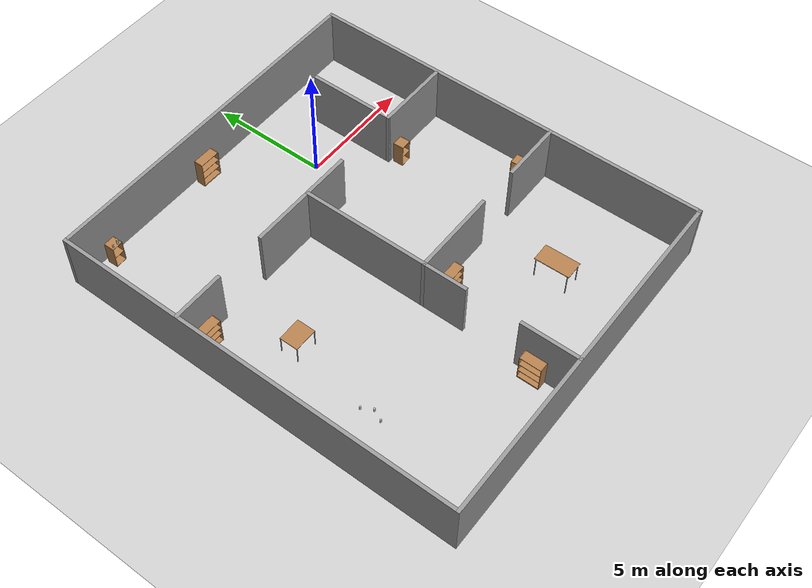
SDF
<sdf version="1.6">
 <world name="default">
  <physics name="default_physics" default="0" type="ode">
   <ode>
    <solver>
     <type>quick</type>
     <iters>20</iters>
     <sor>1</sor>
     <use_dynamic_moi_rescaling>0</use_dynamic_moi_rescaling>
    </solver>
    <constraints>
     <cfm>0</cfm>
     <erp>0.2</erp>
     <contact_max_correcting_vel>100</contact_max_correcting_vel>
     <contact_surface_layer>0</contact_surface_layer>
    </constraints>
   </ode>
   <real_time_update_rate>1000</real_time_update_rate>
   <max_step_size>0.001</max_step_size>
   <real_time_factor>1</real_time_factor>
   <max_contacts>20</max_contacts>
  </physics>
  <light name="sun" type="directional">
   <pose>0 0 10 0 -0 0</pose>
   <diffuse>0.8 0.8 0.8 1</diffuse>
   <specular>0.2 0.2 0.2 1</specular>
   <attenuation>
    <range>1000</range>
    <constant>0.9</constant>
    <linear>0.01</linear>
    <quadratic>0.001</quadratic>
   </attenuation>
   <direction>0.5 0.1 -0.9</direction>
  </light>
  <model name="ground_plane">
   <static>1</static>
   <link name="link">
    <collision name="collision">
     <geometry><plane><normal>0 0 1</normal><size>100 100</size></plane></geometry>
     <surface><friction><ode><mu>100</mu><mu2>50</mu2></ode></friction></surface>
    </collision>
    <visual name="visual">
     <cast_shadows>0</cast_shadows>
     <geometry><plane><normal>0 0 1</normal><size>100 100</size></plane></geometry>
     <material>
      <script><uri>file://media/materials/scripts/gazebo.material</uri><name>Gazebo/Grey</name></script>
     </material>
    </visual>
    <velocity_decay><linear>0</linear><angular>0</angular></velocity_decay>
   </link>
  </model>
  <scene><ambient>0.2 0.2 0.2 1</ambient><background>0.7 0.7 0.7 1</background><shadows>1</shadows></scene>
  <model name="cabinet">
   <static>0</static>
   <link name="cabinet_bottom_plate">
    <inertial>
     <pose>0 0 -1 0 -0 0</pose>
     <inertia><ixx>2.05</ixx><ixy>0</ixy><ixz>0</ixz><iyy>2.05</iyy><iyz>0</iyz><izz>2.05</izz></inertia>
     <mass>25</mass>
    </inertial>
    <collision name="cabinet_bottom_plate_geom">
     <pose>0 0 0.01 0 -0 0</pose>
     <geometry><box><size>0.45 0.45 0.02</size></box></geometry>
    </collision>
    <visual name="cabinet_bottom_plate_geom_visual">
     <pose>0 0 0.01 0 -0 0</pose>
     <geometry><box><size>0.45 0.45 0.02</size></box></geometry>
     <material>
      <script><uri>file://media/materials/scripts/gazebo.material</uri><name>Gazebo/Wood</name></script>
     </material>
    </visual>
    <collision name="cabinet_bottom_plate_geom_cabinet_back_plate">
     <pose>0.235 0 0.51 0 -0 0</pose>
     <geometry><box><size>0.02 0.45 1.02</size></box></geometry>
    </collision>
    <visual name="cabinet_bottom_plate_geom_cabinet_back_plate_visual">
     <pose>0.235 0 0.51 0 -0 0</pose>
     <geometry><box><size>0.02 0.45 1.02</size></box></geometry>
     <material>
      <script><uri>file://media/materials/scripts/gazebo.material</uri><name>Gazebo/Wood</name></script>
     </material>
    </visual>
    <collision name="cabinet_bottom_plate_geom_cabinet_left_plate">
     <pose>0 0.235 0.51 0 -0 0</pose>
     <geometry><box><size>0.45 0.02 1.02</size></box></geometry>
    </collision>
    <visual name="cabinet_bottom_plate_geom_cabinet_left_plate_visual">
     <pose>0 0.235 0.51 0 -0 0</pose>
     <geometry><box><size>0.45 0.02 1.02</size></box></geometry>
     <material>
      <script><uri>file://media/materials/scripts/gazebo.material</uri><name>Gazebo/Wood</name></script>
     </material>
    </visual>
    <collision name="cabinet_bottom_plate_geom_cabinet_middle_plate">
     <pose>0 0 0.51 0 -0 0</pose>
     <geometry><box><size>0.45 0.45 0.02</size></box></geometry>
    </collision>
    <visual name="cabinet_bottom_plate_geom_cabinet_middle_plate_visual">
     <pose>0 0 0.51 0 -0 0</pose>
     <geometry><box><size>0.45 0.45 0.02</size></box></geometry>
     <material>
      <script><uri>file://media/materials/scripts/gazebo.material</uri><name>Gazebo/Wood</name></script>
     </material>
    </visual>
    <collision name="cabinet_bottom_plate_geom_cabinet_right_plate">
     <pose>0 -0.235 0.51 0 -0 0</pose>
     <geometry><box><size>0.45 0.02 1.02</size></box></geometry>
    </collision>
    <visual name="cabinet_bottom_plate_geom_cabinet_right_plate_visual">
     <pose>0 -0.235 0.51 0 -0 0</pose>
     <geometry><box><size>0.45 0.02 1.02</size></box></geometry>
     <material>
      <script><uri>file://media/materials/scripts/gazebo.material</uri><name>Gazebo/Wood</name></script>
     </material>
    </visual>
    <collision name="cabinet_bottom_plate_geom_cabinet_top_plate">
     <pose>0 0 1.01 0 -0 0</pose>
     <geometry><box><size>0.45 0.45 0.02</size></box></geometry>
    </collision>
    <visual name="cabinet_bottom_plate_geom_cabinet_top_plate_visual">
     <pose>0 0 1.01 0 -0 0</pose>
     <geometry><box><size>0.45 0.45 0.02</size></box></geometry>
     <material>
      <script><uri>file://media/materials/scripts/gazebo.material</uri><name>Gazebo/Wood</name></script>
     </material>
    </visual>
    <velocity_decay><linear>0</linear><angular>0</angular></velocity_decay>
   </link>
   <pose>2.45497 -2.41796 0 -1e-06 0 1.59663</pose>
  </model>
  <model name="cabinet_0">
   <static>0</static>
   <link name="cabinet_bottom_plate">
    <inertial>
     <pose>0 0 -1 0 -0 0</pose>
     <inertia><ixx>2.05</ixx><ixy>0</ixy><ixz>0</ixz><iyy>2.05</iyy><iyz>0</iyz><izz>2.05</izz></inertia>
     <mass>25</mass>
    </inertial>
    <collision name="cabinet_bottom_plate_geom">
     <pose>0 0 0.01 0 -0 0</pose>
     <geometry><box><size>0.45 0.45 0.02</size></box></geometry>
    </collision>
    <visual name="cabinet_bottom_plate_geom_visual">
     <pose>0 0 0.01 0 -0 0</pose>
     <geometry><box><size>0.45 0.45 0.02</size></box></geometry>
     <material>
      <script><uri>file://media/materials/scripts/gazebo.material</uri><name>Gazebo/Wood</name></script>
     </material>
    </visual>
    <collision name="cabinet_bottom_plate_geom_cabinet_back_plate">
     <pose>0.235 0 0.51 0 -0 0</pose>
     <geometry><box><size>0.02 0.45 1.02</size></box></geometry>
    </collision>
    <visual name="cabinet_bottom_plate_geom_cabinet_back_plate_visual">
     <pose>0.235 0 0.51 0 -0 0</pose>
     <geometry><box><size>0.02 0.45 1.02</size></box></geometry>
     <material>
      <script><uri>file://media/materials/scripts/gazebo.material</uri><name>Gazebo/Wood</name></script>
     </material>
    </visual>
    <collision name="cabinet_bottom_plate_geom_cabinet_left_plate">
     <pose>0 0.235 0.51 0 -0 0</pose>
     <geometry><box><size>0.45 0.02 1.02</size></box></geometry>
    </collision>
    <visual name="cabinet_bottom_plate_geom_cabinet_left_plate_visual">
     <pose>0 0.235 0.51 0 -0 0</pose>
     <geometry><box><size>0.45 0.02 1.02</size></box></geometry>
     <material>
      <script><uri>file://media/materials/scripts/gazebo.material</uri><name>Gazebo/Wood</name></script>
     </material>
    </visual>
    <collision name="cabinet_bottom_plate_geom_cabinet_middle_plate">
     <pose>0 0 0.51 0 -0 0</pose>
     <geometry><box><size>0.45 0.45 0.02</size></box></geometry>
    </collision>
    <visual name="cabinet_bottom_plate_geom_cabinet_middle_plate_visual">
     <pose>0 0 0.51 0 -0 0</pose>
     <geometry><box><size>0.45 0.45 0.02</size></box></geometry>
     <material>
      <script><uri>file://media/materials/scripts/gazebo.material</uri><name>Gazebo/Wood</name></script>
     </material>
    </visual>
    <collision name="cabinet_bottom_plate_geom_cabinet_right_plate">
     <pose>0 -0.235 0.51 0 -0 0</pose>
     <geometry><box><size>0.45 0.02 1.02</size></box></geometry>
    </collision>
    <visual name="cabinet_bottom_plate_geom_cabinet_right_plate_visual">
     <pose>0 -0.235 0.51 0 -0 0</pose>
     <geometry><box><size>0.45 0.02 1.02</size></box></geometry>
     <material>
      <script><uri>file://media/materials/scripts/gazebo.material</uri><name>Gazebo/Wood</name></script>
     </material>
    </visual>
    <collision name="cabinet_bottom_plate_geom_cabinet_top_plate">
     <pose>0 0 1.01 0 -0 0</pose>
     <geometry><box><size>0.45 0.45 0.02</size></box></geometry>
    </collision>
    <visual name="cabinet_bottom_plate_geom_cabinet_top_plate_visual">
     <pose>0 0 1.01 0 -0 0</pose>
     <geometry><box><size>0.45 0.45 0.02</size></box></geometry>
     <material>
      <script><uri>file://media/materials/scripts/gazebo.material</uri><name>Gazebo/Wood</name></script>
     </material>
    </visual>
    <velocity_decay><linear>0</linear><angular>0</angular></velocity_decay>
   </link>
   <pose>4.50468 -6.65182 0 -1e-06 0 0.01487</pose>
  </model>
  <model name="bookshelf">
   <static>0</static>
   <link name="link">
    <inertial>
     <mass>1</mass>
     <inertia><ixx>1</ixx><ixy>0</ixy><ixz>0</ixz><iyy>1</iyy><iyz>0</iyz><izz>1</izz></inertia>
    </inertial>
    <collision name="back">
     <pose>0 0.005 0.6 0 -0 0</pose>
     <geometry><box><size>0.9 0.01 1.2</size></box></geometry>
    </collision>
    <visual name="visual1">
     <pose>0 0.005 0.6 0 -0 0</pose>
     <geometry><box><size>0.9 0.01 1.2</size></box></geometry>
     <material>
      <script><uri>file://media/materials/scripts/gazebo.material</uri><name>Gazebo/Wood</name></script>
     </material>
    </visual>
    <collision name="left_side">
     <pose>0.45 -0.195 0.6 0 -0 0</pose>
     <geometry><box><size>0.02 0.4 1.2</size></box></geometry>
    </collision>
    <visual name="visual2">
     <pose>0.45 -0.195 0.6 0 -0 0</pose>
     <geometry><box><size>0.02 0.4 1.2</size></box></geometry>
     <material>
      <script><uri>file://media/materials/scripts/gazebo.material</uri><name>Gazebo/Wood</name></script>
     </material>
    </visual>
    <collision name="right_side">
     <pose>-0.45 -0.195 0.6 0 -0 0</pose>
     <geometry><box><size>0.02 0.4 1.2</size></box></geometry>
    </collision>
    <visual name="visual3">
     <pose>-0.45 -0.195 0.6 0 -0 0</pose>
     <geometry><box><size>0.02 0.4 1.2</size></box></geometry>
     <material>
      <script><uri>file://media/materials/scripts/gazebo.material</uri><name>Gazebo/Wood</name></script>
     </material>
    </visual>
    <collision name="bottom">
     <pose>0 -0.195 0.03 0 -0 0</pose>
     <geometry><box><size>0.88 0.4 0.06</size></box></geometry>
    </collision>
    <visual name="visual4">
     <pose>0 -0.195 0.03 0 -0 0</pose>
     <geometry><box><size>0.88 0.4 0.06</size></box></geometry>
     <material>
      <script><uri>file://media/materials/scripts/gazebo.material</uri><name>Gazebo/Wood</name></script>
     </material>
    </visual>
    <collision name="top">
     <pose>0 -0.195 1.19 0 -0 0</pose>
     <geometry><box><size>0.88 0.4 0.02</size></box></geometry>
    </collision>
    <visual name="visual5">
     <pose>0 -0.195 1.19 0 -0 0</pose>
     <geometry><box><size>0.88 0.4 0.02</size></box></geometry>
     <material>
      <script><uri>file://media/materials/scripts/gazebo.material</uri><name>Gazebo/Wood</name></script>
     </material>
    </visual>
    <collision name="low_shelf">
     <pose>0 -0.195 0.43 0 -0 0</pose>
     <geometry><box><size>0.88 0.4 0.02</size></box></geometry>
    </collision>
    <visual name="visual6">
     <pose>0 -0.195 0.43 0 -0 0</pose>
     <geometry><box><size>0.88 0.4 0.02</size></box></geometry>
     <material>
      <script><uri>file://media/materials/scripts/gazebo.material</uri><name>Gazebo/Wood</name></script>
     </material>
    </visual>
    <collision name="high_shelf">
     <pose>0 -0.195 0.8 0 -0 0</pose>
     <geometry><box><size>0.88 0.4 0.02</size></box></geometry>
    </collision>
    <visual name="visual7">
     <pose>0 -0.195 0.8 0 -0 0</pose>
     <geometry><box><size>0.88 0.4 0.02</size></box></geometry>
     <material>
      <script><uri>file://media/materials/scripts/gazebo.material</uri><name>Gazebo/Wood</name></script>
     </material>
    </visual>
    <velocity_decay><linear>0</linear><angular>0</angular></velocity_decay>
   </link>
   <pose>-8.86577 -2.21666 1e-06 -2e-05 -1e-06 0</pose>
  </model>
  <model name="bookshelf_0">
   <static>0</static>
   <link name="link">
    <inertial>
     <mass>1</mass>
     <inertia><ixx>1</ixx><ixy>0</ixy><ixz>0</ixz><iyy>1</iyy><iyz>0</iyz><izz>1</izz></inertia>
    </inertial>
    <collision name="back">
     <pose>0 0.005 0.6 0 -0 0</pose>
     <geometry><box><size>0.9 0.01 1.2</size></box></geometry>
    </collision>
    <visual name="visual1">
     <pose>0 0.005 0.6 0 -0 0</pose>
     <geometry><box><size>0.9 0.01 1.2</size></box></geometry>
     <material>
      <script><uri>file://media/materials/scripts/gazebo.material</uri><name>Gazebo/Wood</name></script>
     </material>
    </visual>
    <collision name="left_side">
     <pose>0.45 -0.195 0.6 0 -0 0</pose>
     <geometry><box><size>0.02 0.4 1.2</size></box></geometry>
    </collision>
    <visual name="visual2">
     <pose>0.45 -0.195 0.6 0 -0 0</pose>
     <geometry><box><size>0.02 0.4 1.2</size></box></geometry>
     <material>
      <script><uri>file://media/materials/scripts/gazebo.material</uri><name>Gazebo/Wood</name></script>
     </material>
    </visual>
    <collision name="right_side">
     <pose>-0.45 -0.195 0.6 0 -0 0</pose>
     <geometry><box><size>0.02 0.4 1.2</size></box></geometry>
    </collision>
    <visual name="visual3">
     <pose>-0.45 -0.195 0.6 0 -0 0</pose>
     <geometry><box><size>0.02 0.4 1.2</size></box></geometry>
     <material>
      <script><uri>file://media/materials/scripts/gazebo.material</uri><name>Gazebo/Wood</name></script>
     </material>
    </visual>
    <collision name="bottom">
     <pose>0 -0.195 0.03 0 -0 0</pose>
     <geometry><box><size>0.88 0.4 0.06</size></box></geometry>
    </collision>
    <visual name="visual4">
     <pose>0 -0.195 0.03 0 -0 0</pose>
     <geometry><box><size>0.88 0.4 0.06</size></box></geometry>
     <material>
      <script><uri>file://media/materials/scripts/gazebo.material</uri><name>Gazebo/Wood</name></script>
     </material>
    </visual>
    <collision name="top">
     <pose>0 -0.195 1.19 0 -0 0</pose>
     <geometry><box><size>0.88 0.4 0.02</size></box></geometry>
    </collision>
    <visual name="visual5">
     <pose>0 -0.195 1.19 0 -0 0</pose>
     <geometry><box><size>0.88 0.4 0.02</size></box></geometry>
     <material>
      <script><uri>file://media/materials/scripts/gazebo.material</uri><name>Gazebo/Wood</name></script>
     </material>
    </visual>
    <collision name="low_shelf">
     <pose>0 -0.195 0.43 0 -0 0</pose>
     <geometry><box><size>0.88 0.4 0.02</size></box></geometry>
    </collision>
    <visual name="visual6">
     <pose>0 -0.195 0.43 0 -0 0</pose>
     <geometry><box><size>0.88 0.4 0.02</size></box></geometry>
     <material>
      <script><uri>file://media/materials/scripts/gazebo.material</uri><name>Gazebo/Wood</name></script>
     </material>
    </visual>
    <collision name="high_shelf">
     <pose>0 -0.195 0.8 0 -0 0</pose>
     <geometry><box><size>0.88 0.4 0.02</size></box></geometry>
    </collision>
    <visual name="visual7">
     <pose>0 -0.195 0.8 0 -0 0</pose>
     <geometry><box><size>0.88 0.4 0.02</size></box></geometry>
     <material>
      <script><uri>file://media/materials/scripts/gazebo.material</uri><name>Gazebo/Wood</name></script>
     </material>
    </visual>
    <velocity_decay><linear>0</linear><angular>0</angular></velocity_decay>
   </link>
   <pose>-3.00014 -1.82706 0 -2.2e-05 0 -3.1216</pose>
  </model>
  <model name="bookshelf_1">
   <static>0</static>
   <link name="link">
    <inertial>
     <mass>1</mass>
     <inertia><ixx>1</ixx><ixy>0</ixy><ixz>0</ixz><iyy>1</iyy><iyz>0</iyz><izz>1</izz></inertia>
    </inertial>
    <collision name="back">
     <pose>0 0.005 0.6 0 -0 0</pose>
     <geometry><box><size>0.9 0.01 1.2</size></box></geometry>
    </collision>
    <visual name="visual1">
     <pose>0 0.005 0.6 0 -0 0</pose>
     <geometry><box><size>0.9 0.01 1.2</size></box></geometry>
     <material>
      <script><uri>file://media/materials/scripts/gazebo.material</uri><name>Gazebo/Wood</name></script>
     </material>
    </visual>
    <collision name="left_side">
     <pose>0.45 -0.195 0.6 0 -0 0</pose>
     <geometry><box><size>0.02 0.4 1.2</size></box></geometry>
    </collision>
    <visual name="visual2">
     <pose>0.45 -0.195 0.6 0 -0 0</pose>
     <geometry><box><size>0.02 0.4 1.2</size></box></geometry>
     <material>
      <script><uri>file://media/materials/scripts/gazebo.material</uri><name>Gazebo/Wood</name></script>
     </material>
    </visual>
    <collision name="right_side">
     <pose>-0.45 -0.195 0.6 0 -0 0</pose>
     <geometry><box><size>0.02 0.4 1.2</size></box></geometry>
    </collision>
    <visual name="visual3">
     <pose>-0.45 -0.195 0.6 0 -0 0</pose>
     <geometry><box><size>0.02 0.4 1.2</size></box></geometry>
     <material>
      <script><uri>file://media/materials/scripts/gazebo.material</uri><name>Gazebo/Wood</name></script>
     </material>
    </visual>
    <collision name="bottom">
     <pose>0 -0.195 0.03 0 -0 0</pose>
     <geometry><box><size>0.88 0.4 0.06</size></box></geometry>
    </collision>
    <visual name="visual4">
     <pose>0 -0.195 0.03 0 -0 0</pose>
     <geometry><box><size>0.88 0.4 0.06</size></box></geometry>
     <material>
      <script><uri>file://media/materials/scripts/gazebo.material</uri><name>Gazebo/Wood</name></script>
     </material>
    </visual>
    <collision name="top">
     <pose>0 -0.195 1.19 0 -0 0</pose>
     <geometry><box><size>0.88 0.4 0.02</size></box></geometry>
    </collision>
    <visual name="visual5">
     <pose>0 -0.195 1.19 0 -0 0</pose>
     <geometry><box><size>0.88 0.4 0.02</size></box></geometry>
     <material>
      <script><uri>file://media/materials/scripts/gazebo.material</uri><name>Gazebo/Wood</name></script>
     </material>
    </visual>
    <collision name="low_shelf">
     <pose>0 -0.195 0.43 0 -0 0</pose>
     <geometry><box><size>0.88 0.4 0.02</size></box></geometry>
    </collision>
    <visual name="visual6">
     <pose>0 -0.195 0.43 0 -0 0</pose>
     <geometry><box><size>0.88 0.4 0.02</size></box></geometry>
     <material>
      <script><uri>file://media/materials/scripts/gazebo.material</uri><name>Gazebo/Wood</name></script>
     </material>
    </visual>
    <collision name="high_shelf">
     <pose>0 -0.195 0.8 0 -0 0</pose>
     <geometry><box><size>0.88 0.4 0.02</size></box></geometry>
    </collision>
    <visual name="visual7">
     <pose>0 -0.195 0.8 0 -0 0</pose>
     <geometry><box><size>0.88 0.4 0.02</size></box></geometry>
     <material>
      <script><uri>file://media/materials/scripts/gazebo.material</uri><name>Gazebo/Wood</name></script>
     </material>
    </visual>
    <velocity_decay><linear>0</linear><angular>0</angular></velocity_decay>
   </link>
   <pose>-2.97644 3.26394 1e-06 -6.7e-05 -0 -0.010391</pose>
  </model>
  <model name="cabinet_1">
   <static>0</static>
   <link name="cabinet_bottom_plate">
    <inertial>
     <pose>0 0 -1 0 -0 0</pose>
     <inertia><ixx>2.05</ixx><ixy>0</ixy><ixz>0</ixz><iyy>2.05</iyy><iyz>0</iyz><izz>2.05</izz></inertia>
     <mass>25</mass>
    </inertial>
    <collision name="cabinet_bottom_plate_geom">
     <pose>0 0 0.01 0 -0 0</pose>
     <geometry><box><size>0.45 0.45 0.02</size></box></geometry>
    </collision>
    <visual name="cabinet_bottom_plate_geom_visual">
     <pose>0 0 0.01 0 -0 0</pose>
     <geometry><box><size>0.45 0.45 0.02</size></box></geometry>
     <material>
      <script><uri>file://media/materials/scripts/gazebo.material</uri><name>Gazebo/Wood</name></script>
     </material>
    </visual>
    <collision name="cabinet_bottom_plate_geom_cabinet_back_plate">
     <pose>0.235 0 0.51 0 -0 0</pose>
     <geometry><box><size>0.02 0.45 1.02</size></box></geometry>
    </collision>
    <visual name="cabinet_bottom_plate_geom_cabinet_back_plate_visual">
     <pose>0.235 0 0.51 0 -0 0</pose>
     <geometry><box><size>0.02 0.45 1.02</size></box></geometry>
     <material>
      <script><uri>file://media/materials/scripts/gazebo.material</uri><name>Gazebo/Wood</name></script>
     </material>
    </visual>
    <collision name="cabinet_bottom_plate_geom_cabinet_left_plate">
     <pose>0 0.235 0.51 0 -0 0</pose>
     <geometry><box><size>0.45 0.02 1.02</size></box></geometry>
    </collision>
    <visual name="cabinet_bottom_plate_geom_cabinet_left_plate_visual">
     <pose>0 0.235 0.51 0 -0 0</pose>
     <geometry><box><size>0.45 0.02 1.02</size></box></geometry>
     <material>
      <script><uri>file://media/materials/scripts/gazebo.material</uri><name>Gazebo/Wood</name></script>
     </material>
    </visual>
    <collision name="cabinet_bottom_plate_geom_cabinet_middle_plate">
     <pose>0 0 0.51 0 -0 0</pose>
     <geometry><box><size>0.45 0.45 0.02</size></box></geometry>
    </collision>
    <visual name="cabinet_bottom_plate_geom_cabinet_middle_plate_visual">
     <pose>0 0 0.51 0 -0 0</pose>
     <geometry><box><size>0.45 0.45 0.02</size></box></geometry>
     <material>
      <script><uri>file://media/materials/scripts/gazebo.material</uri><name>Gazebo/Wood</name></script>
     </material>
    </visual>
    <collision name="cabinet_bottom_plate_geom_cabinet_right_plate">
     <pose>0 -0.235 0.51 0 -0 0</pose>
     <geometry><box><size>0.45 0.02 1.02</size></box></geometry>
    </collision>
    <visual name="cabinet_bottom_plate_geom_cabinet_right_plate_visual">
     <pose>0 -0.235 0.51 0 -0 0</pose>
     <geometry><box><size>0.45 0.02 1.02</size></box></geometry>
     <material>
      <script><uri>file://media/materials/scripts/gazebo.material</uri><name>Gazebo/Wood</name></script>
     </material>
    </visual>
    <collision name="cabinet_bottom_plate_geom_cabinet_top_plate">
     <pose>0 0 1.01 0 -0 0</pose>
     <geometry><box><size>0.45 0.45 0.02</size></box></geometry>
    </collision>
    <visual name="cabinet_bottom_plate_geom_cabinet_top_plate_visual">
     <pose>0 0 1.01 0 -0 0</pose>
     <geometry><box><size>0.45 0.45 0.02</size></box></geometry>
     <material>
      <script><uri>file://media/materials/scripts/gazebo.material</uri><name>Gazebo/Wood</name></script>
     </material>
    </visual>
    <velocity_decay><linear>0</linear><angular>0</angular></velocity_decay>
   </link>
   <pose>-9.33548 -7.30014 0 1e-06 -0 -3.09911</pose>
  </model>
  <model name="cabinet_2">
   <static>0</static>
   <link name="cabinet_bottom_plate">
    <inertial>
     <pose>0 0 -1 0 -0 0</pose>
     <inertia><ixx>2.05</ixx><ixy>0</ixy><ixz>0</ixz><iyy>2.05</iyy><iyz>0</iyz><izz>2.05</izz></inertia>
     <mass>25</mass>
    </inertial>
    <collision name="cabinet_bottom_plate_geom">
     <pose>0 0 0.01 0 -0 0</pose>
     <geometry><box><size>0.45 0.45 0.02</size></box></geometry>
    </collision>
    <visual name="cabinet_bottom_plate_geom_visual">
     <pose>0 0 0.01 0 -0 0</pose>
     <geometry><box><size>0.45 0.45 0.02</size></box></geometry>
     <material>
      <script><uri>file://media/materials/scripts/gazebo.material</uri><name>Gazebo/Wood</name></script>
     </material>
    </visual>
    <collision name="cabinet_bottom_plate_geom_cabinet_back_plate">
     <pose>0.235 0 0.51 0 -0 0</pose>
     <geometry><box><size>0.02 0.45 1.02</size></box></geometry>
    </collision>
    <visual name="cabinet_bottom_plate_geom_cabinet_back_plate_visual">
     <pose>0.235 0 0.51 0 -0 0</pose>
     <geometry><box><size>0.02 0.45 1.02</size></box></geometry>
     <material>
      <script><uri>file://media/materials/scripts/gazebo.material</uri><name>Gazebo/Wood</name></script>
     </material>
    </visual>
    <collision name="cabinet_bottom_plate_geom_cabinet_left_plate">
     <pose>0 0.235 0.51 0 -0 0</pose>
     <geometry><box><size>0.45 0.02 1.02</size></box></geometry>
    </collision>
    <visual name="cabinet_bottom_plate_geom_cabinet_left_plate_visual">
     <pose>0 0.235 0.51 0 -0 0</pose>
     <geometry><box><size>0.45 0.02 1.02</size></box></geometry>
     <material>
      <script><uri>file://media/materials/scripts/gazebo.material</uri><name>Gazebo/Wood</name></script>
     </material>
    </visual>
    <collision name="cabinet_bottom_plate_geom_cabinet_middle_plate">
     <pose>0 0 0.51 0 -0 0</pose>
     <geometry><box><size>0.45 0.45 0.02</size></box></geometry>
    </collision>
    <visual name="cabinet_bottom_plate_geom_cabinet_middle_plate_visual">
     <pose>0 0 0.51 0 -0 0</pose>
     <geometry><box><size>0.45 0.45 0.02</size></box></geometry>
     <material>
      <script><uri>file://media/materials/scripts/gazebo.material</uri><name>Gazebo/Wood</name></script>
     </material>
    </visual>
    <collision name="cabinet_bottom_plate_geom_cabinet_right_plate">
     <pose>0 -0.235 0.51 0 -0 0</pose>
     <geometry><box><size>0.45 0.02 1.02</size></box></geometry>
    </collision>
    <visual name="cabinet_bottom_plate_geom_cabinet_right_plate_visual">
     <pose>0 -0.235 0.51 0 -0 0</pose>
     <geometry><box><size>0.45 0.02 1.02</size></box></geometry>
     <material>
      <script><uri>file://media/materials/scripts/gazebo.material</uri><name>Gazebo/Wood</name></script>
     </material>
    </visual>
    <collision name="cabinet_bottom_plate_geom_cabinet_top_plate">
     <pose>0 0 1.01 0 -0 0</pose>
     <geometry><box><size>0.45 0.45 0.02</size></box></geometry>
    </collision>
    <visual name="cabinet_bottom_plate_geom_cabinet_top_plate_visual">
     <pose>0 0 1.01 0 -0 0</pose>
     <geometry><box><size>0.45 0.45 0.02</size></box></geometry>
     <material>
      <script><uri>file://media/materials/scripts/gazebo.material</uri><name>Gazebo/Wood</name></script>
     </material>
    </visual>
    <velocity_decay><linear>0</linear><angular>0</angular></velocity_decay>
   </link>
   <pose>-8.16988 3.01082 -0.004856 -4e-05 -0.000312 1.59163</pose>
  </model>
  <model name="bookshelf_2">
   <static>0</static>
   <link name="link">
    <inertial>
     <mass>1</mass>
     <inertia><ixx>1</ixx><ixy>0</ixy><ixz>0</ixz><iyy>1</iyy><iyz>0</iyz><izz>1</izz></inertia>
    </inertial>
    <collision name="back">
     <pose>0 0.005 0.6 0 -0 0</pose>
     <geometry><box><size>0.9 0.01 1.2</size></box></geometry>
    </collision>
    <visual name="visual1">
     <pose>0 0.005 0.6 0 -0 0</pose>
     <geometry><box><size>0.9 0.01 1.2</size></box></geometry>
     <material>
      <script><uri>file://media/materials/scripts/gazebo.material</uri><name>Gazebo/Wood</name></script>
     </material>
    </visual>
    <collision name="left_side">
     <pose>0.45 -0.195 0.6 0 -0 0</pose>
     <geometry><box><size>0.02 0.4 1.2</size></box></geometry>
    </collision>
    <visual name="visual2">
     <pose>0.45 -0.195 0.6 0 -0 0</pose>
     <geometry><box><size>0.02 0.4 1.2</size></box></geometry>
     <material>
      <script><uri>file://media/materials/scripts/gazebo.material</uri><name>Gazebo/Wood</name></script>
     </material>
    </visual>
    <collision name="right_side">
     <pose>-0.45 -0.195 0.6 0 -0 0</pose>
     <geometry><box><size>0.02 0.4 1.2</size></box></geometry>
    </collision>
    <visual name="visual3">
     <pose>-0.45 -0.195 0.6 0 -0 0</pose>
     <geometry><box><size>0.02 0.4 1.2</size></box></geometry>
     <material>
      <script><uri>file://media/materials/scripts/gazebo.material</uri><name>Gazebo/Wood</name></script>
     </material>
    </visual>
    <collision name="bottom">
     <pose>0 -0.195 0.03 0 -0 0</pose>
     <geometry><box><size>0.88 0.4 0.06</size></box></geometry>
    </collision>
    <visual name="visual4">
     <pose>0 -0.195 0.03 0 -0 0</pose>
     <geometry><box><size>0.88 0.4 0.06</size></box></geometry>
     <material>
      <script><uri>file://media/materials/scripts/gazebo.material</uri><name>Gazebo/Wood</name></script>
     </material>
    </visual>
    <collision name="top">
     <pose>0 -0.195 1.19 0 -0 0</pose>
     <geometry><box><size>0.88 0.4 0.02</size></box></geometry>
    </collision>
    <visual name="visual5">
     <pose>0 -0.195 1.19 0 -0 0</pose>
     <geometry><box><size>0.88 0.4 0.02</size></box></geometry>
     <material>
      <script><uri>file://media/materials/scripts/gazebo.material</uri><name>Gazebo/Wood</name></script>
     </material>
    </visual>
    <collision name="low_shelf">
     <pose>0 -0.195 0.43 0 -0 0</pose>
     <geometry><box><size>0.88 0.4 0.02</size></box></geometry>
    </collision>
    <visual name="visual6">
     <pose>0 -0.195 0.43 0 -0 0</pose>
     <geometry><box><size>0.88 0.4 0.02</size></box></geometry>
     <material>
      <script><uri>file://media/materials/scripts/gazebo.material</uri><name>Gazebo/Wood</name></script>
     </material>
    </visual>
    <collision name="high_shelf">
     <pose>0 -0.195 0.8 0 -0 0</pose>
     <geometry><box><size>0.88 0.4 0.02</size></box></geometry>
    </collision>
    <visual name="visual7">
     <pose>0 -0.195 0.8 0 -0 0</pose>
     <geometry><box><size>0.88 0.4 0.02</size></box></geometry>
     <material>
      <script><uri>file://media/materials/scripts/gazebo.material</uri><name>Gazebo/Wood</name></script>
     </material>
    </visual>
    <velocity_decay><linear>0</linear><angular>0</angular></velocity_decay>
   </link>
   <pose>-2.84756 -12.3107 0 -1.6e-05 0 -1.57079</pose>
  </model>
  <model name="table_0">
   <static>0</static>
   <link name="link">
    <collision name="surface">
     <pose>0 0 1 0 -0 0</pose>
     <geometry><box><size>1.5 0.8 0.03</size></box></geometry>
    </collision>
    <visual name="visual1">
     <pose>0 0 1 0 -0 0</pose>
     <geometry><box><size>1.5 0.8 0.03</size></box></geometry>
     <material>
      <script><uri>file://media/materials/scripts/gazebo.material</uri><name>Gazebo/Wood</name></script>
     </material>
    </visual>
    <collision name="front_left_leg">
     <pose>0.68 0.38 0.5 0 -0 0</pose>
     <geometry><cylinder><radius>0.02</radius><length>1</length></cylinder></geometry>
    </collision>
    <visual name="front_left_leg">
     <pose>0.68 0.38 0.5 0 -0 0</pose>
     <geometry><cylinder><radius>0.02</radius><length>1</length></cylinder></geometry>
     <material>
      <script><uri>file://media/materials/scripts/gazebo.material</uri><name>Gazebo/Grey</name></script>
     </material>
    </visual>
    <collision name="front_right_leg">
     <pose>0.68 -0.38 0.5 0 -0 0</pose>
     <geometry><cylinder><radius>0.02</radius><length>1</length></cylinder></geometry>
    </collision>
    <visual name="front_right_leg">
     <pose>0.68 -0.38 0.5 0 -0 0</pose>
     <geometry><cylinder><radius>0.02</radius><length>1</length></cylinder></geometry>
     <material>
      <script><uri>file://media/materials/scripts/gazebo.material</uri><name>Gazebo/Grey</name></script>
     </material>
    </visual>
    <collision name="back_right_leg">
     <pose>-0.68 -0.38 0.5 0 -0 0</pose>
     <geometry><cylinder><radius>0.02</radius><length>1</length></cylinder></geometry>
    </collision>
    <visual name="back_right_leg">
     <pose>-0.68 -0.38 0.5 0 -0 0</pose>
     <geometry><cylinder><radius>0.02</radius><length>1</length></cylinder></geometry>
     <material>
      <script><uri>file://media/materials/scripts/gazebo.material</uri><name>Gazebo/Grey</name></script>
     </material>
    </visual>
    <collision name="back_left_leg">
     <pose>-0.68 0.38 0.5 0 -0 0</pose>
     <geometry><cylinder><radius>0.02</radius><length>1</length></cylinder></geometry>
    </collision>
    <visual name="back_left_leg">
     <pose>-0.68 0.38 0.5 0 -0 0</pose>
     <geometry><cylinder><radius>0.02</radius><length>1</length></cylinder></geometry>
     <material>
      <script><uri>file://media/materials/scripts/gazebo.material</uri><name>Gazebo/Grey</name></script>
     </material>
    </visual>
    <velocity_decay><linear>0</linear><angular>0</angular></velocity_decay>
    <inertial>
     <inertia><ixx>1</ixx><ixy>0</ixy><ixz>0</ixz><iyy>1</iyy><iyz>0</iyz><izz>1</izz></inertia>
     <mass>1</mass>
    </inertial>
   </link>
   <pose>1.24657 -10.5378 -1e-06 0 1e-06 1.58692</pose>
  </model>
  <model name="cabinet_3">
   <static>0</static>
   <link name="cabinet_bottom_plate">
    <inertial>
     <pose>0 0 -1 0 -0 0</pose>
     <inertia><ixx>2.05</ixx><ixy>0</ixy><ixz>0</ixz><iyy>2.05</iyy><iyz>0</iyz><izz>2.05</izz></inertia>
     <mass>25</mass>
    </inertial>
    <collision name="cabinet_bottom_plate_geom">
     <pose>0 0 0.01 0 -0 0</pose>
     <geometry><box><size>0.45 0.45 0.02</size></box></geometry>
    </collision>
    <visual name="cabinet_bottom_plate_geom_visual">
     <pose>0 0 0.01 0 -0 0</pose>
     <geometry><box><size>0.45 0.45 0.02</size></box></geometry>
     <material>
      <script><uri>file://media/materials/scripts/gazebo.material</uri><name>Gazebo/Wood</name></script>
     </material>
    </visual>
    <collision name="cabinet_bottom_plate_geom_cabinet_back_plate">
     <pose>0.235 0 0.51 0 -0 0</pose>
     <geometry><box><size>0.02 0.45 1.02</size></box></geometry>
    </collision>
    <visual name="cabinet_bottom_plate_geom_cabinet_back_plate_visual">
     <pose>0.235 0 0.51 0 -0 0</pose>
     <geometry><box><size>0.02 0.45 1.02</size></box></geometry>
     <material>
      <script><uri>file://media/materials/scripts/gazebo.material</uri><name>Gazebo/Wood</name></script>
     </material>
    </visual>
    <collision name="cabinet_bottom_plate_geom_cabinet_left_plate">
     <pose>0 0.235 0.51 0 -0 0</pose>
     <geometry><box><size>0.45 0.02 1.02</size></box></geometry>
    </collision>
    <visual name="cabinet_bottom_plate_geom_cabinet_left_plate_visual">
     <pose>0 0.235 0.51 0 -0 0</pose>
     <geometry><box><size>0.45 0.02 1.02</size></box></geometry>
     <material>
      <script><uri>file://media/materials/scripts/gazebo.material</uri><name>Gazebo/Wood</name></script>
     </material>
    </visual>
    <collision name="cabinet_bottom_plate_geom_cabinet_middle_plate">
     <pose>0 0 0.51 0 -0 0</pose>
     <geometry><box><size>0.45 0.45 0.02</size></box></geometry>
    </collision>
    <visual name="cabinet_bottom_plate_geom_cabinet_middle_plate_visual">
     <pose>0 0 0.51 0 -0 0</pose>
     <geometry><box><size>0.45 0.45 0.02</size></box></geometry>
     <material>
      <script><uri>file://media/materials/scripts/gazebo.material</uri><name>Gazebo/Wood</name></script>
     </material>
    </visual>
    <collision name="cabinet_bottom_plate_geom_cabinet_right_plate">
     <pose>0 -0.235 0.51 0 -0 0</pose>
     <geometry><box><size>0.45 0.02 1.02</size></box></geometry>
    </collision>
    <visual name="cabinet_bottom_plate_geom_cabinet_right_plate_visual">
     <pose>0 -0.235 0.51 0 -0 0</pose>
     <geometry><box><size>0.45 0.02 1.02</size></box></geometry>
     <material>
      <script><uri>file://media/materials/scripts/gazebo.material</uri><name>Gazebo/Wood</name></script>
     </material>
    </visual>
    <collision name="cabinet_bottom_plate_geom_cabinet_top_plate">
     <pose>0 0 1.01 0 -0 0</pose>
     <geometry><box><size>0.45 0.45 0.02</size></box></geometry>
    </collision>
    <visual name="cabinet_bottom_plate_geom_cabinet_top_plate_visual">
     <pose>0 0 1.01 0 -0 0</pose>
     <geometry><box><size>0.45 0.45 0.02</size></box></geometry>
     <material>
      <script><uri>file://media/materials/scripts/gazebo.material</uri><name>Gazebo/Wood</name></script>
     </material>
    </visual>
    <velocity_decay><linear>0</linear><angular>0</angular></velocity_decay>
   </link>
   <pose>-8.14197 -1.51823 -0.004573 4.5e-05 -0.000156 -1.54349</pose>
  </model>
  <model name="bookshelf_3">
   <static>0</static>
   <link name="link">
    <inertial>
     <mass>1</mass>
     <inertia><ixx>1</ixx><ixy>0</ixy><ixz>0</ixz><iyy>1</iyy><iyz>0</iyz><izz>1</izz></inertia>
    </inertial>
    <collision name="back">
     <pose>0 0.005 0.6 0 -0 0</pose>
     <geometry><box><size>0.9 0.01 1.2</size></box></geometry>
    </collision>
    <visual name="visual1">
     <pose>0 0.005 0.6 0 -0 0</pose>
     <geometry><box><size>0.9 0.01 1.2</size></box></geometry>
     <material>
      <script><uri>file://media/materials/scripts/gazebo.material</uri><name>Gazebo/Wood</name></script>
     </material>
    </visual>
    <collision name="left_side">
     <pose>0.45 -0.195 0.6 0 -0 0</pose>
     <geometry><box><size>0.02 0.4 1.2</size></box></geometry>
    </collision>
    <visual name="visual2">
     <pose>0.45 -0.195 0.6 0 -0 0</pose>
     <geometry><box><size>0.02 0.4 1.2</size></box></geometry>
     <material>
      <script><uri>file://media/materials/scripts/gazebo.material</uri><name>Gazebo/Wood</name></script>
     </material>
    </visual>
    <collision name="right_side">
     <pose>-0.45 -0.195 0.6 0 -0 0</pose>
     <geometry><box><size>0.02 0.4 1.2</size></box></geometry>
    </collision>
    <visual name="visual3">
     <pose>-0.45 -0.195 0.6 0 -0 0</pose>
     <geometry><box><size>0.02 0.4 1.2</size></box></geometry>
     <material>
      <script><uri>file://media/materials/scripts/gazebo.material</uri><name>Gazebo/Wood</name></script>
     </material>
    </visual>
    <collision name="bottom">
     <pose>0 -0.195 0.03 0 -0 0</pose>
     <geometry><box><size>0.88 0.4 0.06</size></box></geometry>
    </collision>
    <visual name="visual4">
     <pose>0 -0.195 0.03 0 -0 0</pose>
     <geometry><box><size>0.88 0.4 0.06</size></box></geometry>
     <material>
      <script><uri>file://media/materials/scripts/gazebo.material</uri><name>Gazebo/Wood</name></script>
     </material>
    </visual>
    <collision name="top">
     <pose>0 -0.195 1.19 0 -0 0</pose>
     <geometry><box><size>0.88 0.4 0.02</size></box></geometry>
    </collision>
    <visual name="visual5">
     <pose>0 -0.195 1.19 0 -0 0</pose>
     <geometry><box><size>0.88 0.4 0.02</size></box></geometry>
     <material>
      <script><uri>file://media/materials/scripts/gazebo.material</uri><name>Gazebo/Wood</name></script>
     </material>
    </visual>
    <collision name="low_shelf">
     <pose>0 -0.195 0.43 0 -0 0</pose>
     <geometry><box><size>0.88 0.4 0.02</size></box></geometry>
    </collision>
    <visual name="visual6">
     <pose>0 -0.195 0.43 0 -0 0</pose>
     <geometry><box><size>0.88 0.4 0.02</size></box></geometry>
     <material>
      <script><uri>file://media/materials/scripts/gazebo.material</uri><name>Gazebo/Wood</name></script>
     </material>
    </visual>
    <collision name="high_shelf">
     <pose>0 -0.195 0.8 0 -0 0</pose>
     <geometry><box><size>0.88 0.4 0.02</size></box></geometry>
    </collision>
    <visual name="visual7">
     <pose>0 -0.195 0.8 0 -0 0</pose>
     <geometry><box><size>0.88 0.4 0.02</size></box></geometry>
     <material>
      <script><uri>file://media/materials/scripts/gazebo.material</uri><name>Gazebo/Wood</name></script>
     </material>
    </visual>
    <velocity_decay><linear>0</linear><angular>0</angular></velocity_decay>
   </link>
   <pose>-1.6513 -7.6424 1e-06 -3.9e-05 -2e-06 0</pose>
  </model>
  <model name="bookshelf_4">
   <static>0</static>
   <link name="link">
    <inertial>
     <mass>1</mass>
     <inertia><ixx>1</ixx><ixy>0</ixy><ixz>0</ixz><iyy>1</iyy><iyz>0</iyz><izz>1</izz></inertia>
    </inertial>
    <collision name="back">
     <pose>0 0.005 0.6 0 -0 0</pose>
     <geometry><box><size>0.9 0.01 1.2</size></box></geometry>
    </collision>
    <visual name="visual1">
     <pose>0 0.005 0.6 0 -0 0</pose>
     <geometry><box><size>0.9 0.01 1.2</size></box></geometry>
     <material>
      <script><uri>file://media/materials/scripts/gazebo.material</uri><name>Gazebo/Wood</name></script>
     </material>
    </visual>
    <collision name="left_side">
     <pose>0.45 -0.195 0.6 0 -0 0</pose>
     <geometry><box><size>0.02 0.4 1.2</size></box></geometry>
    </collision>
    <visual name="visual2">
     <pose>0.45 -0.195 0.6 0 -0 0</pose>
     <geometry><box><size>0.02 0.4 1.2</size></box></geometry>
     <material>
      <script><uri>file://media/materials/scripts/gazebo.material</uri><name>Gazebo/Wood</name></script>
     </material>
    </visual>
    <collision name="right_side">
     <pose>-0.45 -0.195 0.6 0 -0 0</pose>
     <geometry><box><size>0.02 0.4 1.2</size></box></geometry>
    </collision>
    <visual name="visual3">
     <pose>-0.45 -0.195 0.6 0 -0 0</pose>
     <geometry><box><size>0.02 0.4 1.2</size></box></geometry>
     <material>
      <script><uri>file://media/materials/scripts/gazebo.material</uri><name>Gazebo/Wood</name></script>
     </material>
    </visual>
    <collision name="bottom">
     <pose>0 -0.195 0.03 0 -0 0</pose>
     <geometry><box><size>0.88 0.4 0.06</size></box></geometry>
    </collision>
    <visual name="visual4">
     <pose>0 -0.195 0.03 0 -0 0</pose>
     <geometry><box><size>0.88 0.4 0.06</size></box></geometry>
     <material>
      <script><uri>file://media/materials/scripts/gazebo.material</uri><name>Gazebo/Wood</name></script>
     </material>
    </visual>
    <collision name="top">
     <pose>0 -0.195 1.19 0 -0 0</pose>
     <geometry><box><size>0.88 0.4 0.02</size></box></geometry>
    </collision>
    <visual name="visual5">
     <pose>0 -0.195 1.19 0 -0 0</pose>
     <geometry><box><size>0.88 0.4 0.02</size></box></geometry>
     <material>
      <script><uri>file://media/materials/scripts/gazebo.material</uri><name>Gazebo/Wood</name></script>
     </material>
    </visual>
    <collision name="low_shelf">
     <pose>0 -0.195 0.43 0 -0 0</pose>
     <geometry><box><size>0.88 0.4 0.02</size></box></geometry>
    </collision>
    <visual name="visual6">
     <pose>0 -0.195 0.43 0 -0 0</pose>
     <geometry><box><size>0.88 0.4 0.02</size></box></geometry>
     <material>
      <script><uri>file://media/materials/scripts/gazebo.material</uri><name>Gazebo/Wood</name></script>
     </material>
    </visual>
    <collision name="high_shelf">
     <pose>0 -0.195 0.8 0 -0 0</pose>
     <geometry><box><size>0.88 0.4 0.02</size></box></geometry>
    </collision>
    <visual name="visual7">
     <pose>0 -0.195 0.8 0 -0 0</pose>
     <geometry><box><size>0.88 0.4 0.02</size></box></geometry>
     <material>
      <script><uri>file://media/materials/scripts/gazebo.material</uri><name>Gazebo/Wood</name></script>
     </material>
    </visual>
    <velocity_decay><linear>0</linear><angular>0</angular></velocity_decay>
   </link>
   <pose>4.47222 -1.66795 1e-06 -7e-05 0 3.13785</pose>
  </model>
  <model name="cabinet_4">
   <static>0</static>
   <link name="cabinet_bottom_plate">
    <inertial>
     <pose>0 0 -1 0 -0 0</pose>
     <inertia><ixx>2.05</ixx><ixy>0</ixy><ixz>0</ixz><iyy>2.05</iyy><iyz>0</iyz><izz>2.05</izz></inertia>
     <mass>25</mass>
    </inertial>
    <collision name="cabinet_bottom_plate_geom">
     <pose>0 0 0.01 0 -0 0</pose>
     <geometry><box><size>0.45 0.45 0.02</size></box></geometry>
    </collision>
    <visual name="cabinet_bottom_plate_geom_visual">
     <pose>0 0 0.01 0 -0 0</pose>
     <geometry><box><size>0.45 0.45 0.02</size></box></geometry>
     <material>
      <script><uri>file://media/materials/scripts/gazebo.material</uri><name>Gazebo/Wood</name></script>
     </material>
    </visual>
    <collision name="cabinet_bottom_plate_geom_cabinet_back_plate">
     <pose>0.235 0 0.51 0 -0 0</pose>
     <geometry><box><size>0.02 0.45 1.02</size></box></geometry>
    </collision>
    <visual name="cabinet_bottom_plate_geom_cabinet_back_plate_visual">
     <pose>0.235 0 0.51 0 -0 0</pose>
     <geometry><box><size>0.02 0.45 1.02</size></box></geometry>
     <material>
      <script><uri>file://media/materials/scripts/gazebo.material</uri><name>Gazebo/Wood</name></script>
     </material>
    </visual>
    <collision name="cabinet_bottom_plate_geom_cabinet_left_plate">
     <pose>0 0.235 0.51 0 -0 0</pose>
     <geometry><box><size>0.45 0.02 1.02</size></box></geometry>
    </collision>
    <visual name="cabinet_bottom_plate_geom_cabinet_left_plate_visual">
     <pose>0 0.235 0.51 0 -0 0</pose>
     <geometry><box><size>0.45 0.02 1.02</size></box></geometry>
     <material>
      <script><uri>file://media/materials/scripts/gazebo.material</uri><name>Gazebo/Wood</name></script>
     </material>
    </visual>
    <collision name="cabinet_bottom_plate_geom_cabinet_middle_plate">
     <pose>0 0 0.51 0 -0 0</pose>
     <geometry><box><size>0.45 0.45 0.02</size></box></geometry>
    </collision>
    <visual name="cabinet_bottom_plate_geom_cabinet_middle_plate_visual">
     <pose>0 0 0.51 0 -0 0</pose>
     <geometry><box><size>0.45 0.45 0.02</size></box></geometry>
     <material>
      <script><uri>file://media/materials/scripts/gazebo.material</uri><name>Gazebo/Wood</name></script>
     </material>
    </visual>
    <collision name="cabinet_bottom_plate_geom_cabinet_right_plate">
     <pose>0 -0.235 0.51 0 -0 0</pose>
     <geometry><box><size>0.45 0.02 1.02</size></box></geometry>
    </collision>
    <visual name="cabinet_bottom_plate_geom_cabinet_right_plate_visual">
     <pose>0 -0.235 0.51 0 -0 0</pose>
     <geometry><box><size>0.45 0.02 1.02</size></box></geometry>
     <material>
      <script><uri>file://media/materials/scripts/gazebo.material</uri><name>Gazebo/Wood</name></script>
     </material>
    </visual>
    <collision name="cabinet_bottom_plate_geom_cabinet_top_plate">
     <pose>0 0 1.01 0 -0 0</pose>
     <geometry><box><size>0.45 0.45 0.02</size></box></geometry>
    </collision>
    <visual name="cabinet_bottom_plate_geom_cabinet_top_plate_visual">
     <pose>0 0 1.01 0 -0 0</pose>
     <geometry><box><size>0.45 0.45 0.02</size></box></geometry>
     <material>
      <script><uri>file://media/materials/scripts/gazebo.material</uri><name>Gazebo/Wood</name></script>
     </material>
    </visual>
    <velocity_decay><linear>0</linear><angular>0</angular></velocity_decay>
   </link>
   <pose>-9.29938 -13.4113 0 0 1e-06 -3.14156</pose>
  </model>
  <gravity>0 0 -9.81</gravity>
  <magnetic_field>6e-06 2.3e-05 -4.2e-05</magnetic_field>
  <atmosphere type="adiabatic"/>
  <spherical_coordinates>
   <surface_model>EARTH_WGS84</surface_model>
   <latitude_deg>0</latitude_deg>
   <longitude_deg>0</longitude_deg>
   <elevation>0</elevation>
   <heading_deg>0</heading_deg>
  </spherical_coordinates>
  <model name="cocacola">
   <static>0</static>
   <link name="link">
    <inertial>
     <mass>0.25</mass>
     <inertia><ixx>0</ixx><ixy>0</ixy><ixz>0</ixz><iyy>0</iyy><iyz>0</iyz><izz>0</izz></inertia>
    </inertial>
    <collision name="collision">
     <pose>0 0 0.075 -3.14159 -0 0</pose>
     <geometry><cylinder><radius>0.04</radius><length>0.15</length></cylinder></geometry>
    </collision>
    <visual name="visual">
     <pose>0 0 0.075 -3.14159 -0 0</pose>
     <geometry><cylinder><radius>0.04</radius><length>0.15</length></cylinder></geometry>
     <material>
      <script>
       <uri>model://cocacola/material/scripts</uri>
       <uri>model://cocacola/material/textures</uri>
       <name>Custom/cocacola</name>
      </script>
     </material>
    </visual>
    <velocity_decay><linear>0</linear><angular>0</angular></velocity_decay>
   </link>
   <pose>-7.77263 -9.29055 0.300008 6.4e-05 -0.000189 -4e-06</pose>
  </model>
  <model name="cocacola_0">
   <static>0</static>
   <link name="link">
    <inertial>
     <mass>0.25</mass>
     <inertia><ixx>0</ixx><ixy>0</ixy><ixz>0</ixz><iyy>0</iyy><iyz>0</iyz><izz>0</izz></inertia>
    </inertial>
    <collision name="collision">
     <pose>0 0 0.075 -3.14159 -0 0</pose>
     <geometry><cylinder><radius>0.04</radius><length>0.15</length></cylinder></geometry>
    </collision>
    <visual name="visual">
     <pose>0 0 0.075 -3.14159 -0 0</pose>
     <geometry><cylinder><radius>0.04</radius><length>0.15</length></cylinder></geometry>
     <material>
      <script>
       <uri>model://cocacola/material/scripts</uri>
       <uri>model://cocacola/material/textures</uri>
       <name>Custom/cocacola</name>
      </script>
     </material>
    </visual>
    <velocity_decay><linear>0</linear><angular>0</angular></velocity_decay>
   </link>
   <pose>-7.79476 -8.41563 0.299998 0.000184 -7.5e-05 -2e-06</pose>
  </model>
  <model name="cocacola_1">
   <static>0</static>
   <link name="link">
    <inertial>
     <mass>0.25</mass>
     <inertia><ixx>0</ixx><ixy>0</ixy><ixz>0</ixz><iyy>0</iyy><iyz>0</iyz><izz>0</izz></inertia>
    </inertial>
    <collision name="collision">
     <pose>0 0 0.075 -3.14159 -0 0</pose>
     <geometry><cylinder><radius>0.04</radius><length>0.15</length></cylinder></geometry>
    </collision>
    <visual name="visual">
     <pose>0 0 0.075 -3.14159 -0 0</pose>
     <geometry><cylinder><radius>0.04</radius><length>0.15</length></cylinder></geometry>
     <material>
      <script>
       <uri>model://cocacola/material/scripts</uri>
       <uri>model://cocacola/material/textures</uri>
       <name>Custom/cocacola</name>
      </script>
     </material>
    </visual>
    <velocity_decay><linear>0</linear><angular>0</angular></velocity_decay>
   </link>
   <pose>-7.55915 -8.84989 0.300008 0.000166 -0.000129 1.9e-05</pose>
  </model>
  <model name="cabinet_1">
   <static>0</static>
   <link name="cabinet_bottom_plate">
    <inertial>
     <pose>0 0 -1 0 -0 0</pose>
     <inertia><ixx>2.05</ixx><ixy>0</ixy><ixz>0</ixz><iyy>2.05</iyy><iyz>0</iyz><izz>2.05</izz></inertia>
     <mass>25</mass>
    </inertial>
    <collision name="cabinet_bottom_plate_geom">
     <pose>0 0 0.01 0 -0 0</pose>
     <geometry><box><size>0.45 0.45 0.02</size></box></geometry>
    </collision>
    <visual name="cabinet_bottom_plate_geom_visual">
     <pose>0 0 0.01 0 -0 0</pose>
     <geometry><box><size>0.45 0.45 0.02</size></box></geometry>
     <material>
      <script><uri>file://media/materials/scripts/gazebo.material</uri><name>Gazebo/Wood</name></script>
     </material>
    </visual>
    <collision name="cabinet_bottom_plate_geom_cabinet_back_plate">
     <pose>0.235 0 0.51 0 -0 0</pose>
     <geometry><box><size>0.02 0.45 1.02</size></box></geometry>
    </collision>
    <visual name="cabinet_bottom_plate_geom_cabinet_back_plate_visual">
     <pose>0.235 0 0.51 0 -0 0</pose>
     <geometry><box><size>0.02 0.45 1.02</size></box></geometry>
     <material>
      <script><uri>file://media/materials/scripts/gazebo.material</uri><name>Gazebo/Wood</name></script>
     </material>
    </visual>
    <collision name="cabinet_bottom_plate_geom_cabinet_left_plate">
     <pose>0 0.235 0.51 0 -0 0</pose>
     <geometry><box><size>0.45 0.02 1.02</size></box></geometry>
    </collision>
    <visual name="cabinet_bottom_plate_geom_cabinet_left_plate_visual">
     <pose>0 0.235 0.51 0 -0 0</pose>
     <geometry><box><size>0.45 0.02 1.02</size></box></geometry>
     <material>
      <script><uri>file://media/materials/scripts/gazebo.material</uri><name>Gazebo/Wood</name></script>
     </material>
    </visual>
    <collision name="cabinet_bottom_plate_geom_cabinet_middle_plate">
     <pose>0 0 0.51 0 -0 0</pose>
     <geometry><box><size>0.45 0.45 0.02</size></box></geometry>
    </collision>
    <visual name="cabinet_bottom_plate_geom_cabinet_middle_plate_visual">
     <pose>0 0 0.51 0 -0 0</pose>
     <geometry><box><size>0.45 0.45 0.02</size></box></geometry>
     <material>
      <script><uri>file://media/materials/scripts/gazebo.material</uri><name>Gazebo/Wood</name></script>
     </material>
    </visual>
    <collision name="cabinet_bottom_plate_geom_cabinet_right_plate">
     <pose>0 -0.235 0.51 0 -0 0</pose>
     <geometry><box><size>0.45 0.02 1.02</size></box></geometry>
    </collision>
    <visual name="cabinet_bottom_plate_geom_cabinet_right_plate_visual">
     <pose>0 -0.235 0.51 0 -0 0</pose>
     <geometry><box><size>0.45 0.02 1.02</size></box></geometry>
     <material>
      <script><uri>file://media/materials/scripts/gazebo.material</uri><name>Gazebo/Wood</name></script>
     </material>
    </visual>
    <collision name="cabinet_bottom_plate_geom_cabinet_top_plate">
     <pose>0 0 1.01 0 -0 0</pose>
     <geometry><box><size>0.45 0.45 0.02</size></box></geometry>
    </collision>
    <visual name="cabinet_bottom_plate_geom_cabinet_top_plate_visual">
     <pose>0 0 1.01 0 -0 0</pose>
     <geometry><box><size>0.45 0.45 0.02</size></box></geometry>
     <material>
      <script><uri>file://media/materials/scripts/gazebo.material</uri><name>Gazebo/Wood</name></script>
     </material>
    </visual>
    <velocity_decay><linear>0</linear><angular>0</angular></velocity_decay>
   </link>
   <pose>-9.33548 -7.30014 0 1e-06 -0 -3.09911</pose>
  </model>
  <model name="home_walls">
   <pose>-2.23267 -5.22797 0 0 -0 0</pose>
   <link name="Wall_10">
    <collision name="Wall_10_Collision">
     <geometry><box><size>15.25 0.15 2.5</size></box></geometry>
     <pose>0 0 1.25 0 -0 0</pose>
    </collision>
    <visual name="Wall_10_Visual">
     <pose>0 0 1.25 0 -0 0</pose>
     <geometry><box><size>15.25 0.15 2.5</size></box></geometry>
     <material>
      <script><uri>file://media/materials/scripts/gazebo.material</uri><name>Gazebo/Grey</name></script>
      <ambient>1 1 1 1</ambient>
     </material>
     <meta><layer>0</layer></meta>
    </visual>
    <pose>0 8.675 0 0 -0 3.14159</pose>
   </link>
   <link name="Wall_14">
    <collision name="Wall_14_Collision">
     <geometry><box><size>3.25 0.15 2.5</size></box></geometry>
     <pose>0 0 1.25 0 -0 0</pose>
    </collision>
    <visual name="Wall_14_Visual">
     <pose>0 0 1.25 0 -0 0</pose>
     <geometry><box><size>3.25 0.15 2.5</size></box></geometry>
     <material>
      <script><uri>file://media/materials/scripts/gazebo.material</uri><name>Gazebo/Grey</name></script>
      <ambient>1 1 1 1</ambient>
     </material>
     <meta><layer>0</layer></meta>
    </visual>
    <pose>5.88616 3.20782 0 0 -0 0</pose>
   </link>
   <link name="Wall_16">
    <collision name="Wall_16_Collision">
     <geometry><box><size>3.75 0.15 2.5</size></box></geometry>
     <pose>0 0 1.25 0 -0 0</pose>
    </collision>
    <visual name="Wall_16_Visual">
     <pose>0 0 1.25 0 -0 0</pose>
     <geometry><box><size>3.75 0.15 2.5</size></box></geometry>
     <material>
      <script><uri>file://media/materials/scripts/gazebo.material</uri><name>Gazebo/Grey</name></script>
      <ambient>1 1 1 1</ambient>
     </material>
     <meta><layer>0</layer></meta>
    </visual>
    <pose>4.33616 5.00782 0 0 -0 1.5708</pose>
   </link>
   <link name="Wall_18">
    <collision name="Wall_18_Collision">
     <geometry><box><size>4.75 0.15 2.5</size></box></geometry>
     <pose>0 0 1.25 0 -0 0</pose>
    </collision>
    <visual name="Wall_18_Visual">
     <pose>0 0 1.25 0 -0 0</pose>
     <geometry><box><size>4.75 0.15 2.5</size></box></geometry>
     <material>
      <script><uri>file://media/materials/scripts/gazebo.material</uri><name>Gazebo/Grey</name></script>
      <ambient>1 1 1 1</ambient>
     </material>
     <meta><layer>0</layer></meta>
    </visual>
    <pose>-0.848613 3.23707 0 0 -0 3.14159</pose>
   </link>
   <link name="Wall_20">
    <collision name="Wall_20_Collision">
     <geometry><box><size>2.25 0.15 2.5</size></box></geometry>
     <pose>0 0 1.25 0 -0 0</pose>
    </collision>
    <visual name="Wall_20_Visual">
     <pose>0 0 1.25 0 -0 0</pose>
     <geometry><box><size>2.25 0.15 2.5</size></box></geometry>
     <material>
      <script><uri>file://media/materials/scripts/gazebo.material</uri><name>Gazebo/Grey</name></script>
      <ambient>1 1 1 1</ambient>
     </material>
     <meta><layer>0</layer></meta>
    </visual>
    <pose>-6.48476 3.23707 0 0 -0 0</pose>
   </link>
   <link name="Wall_25">
    <collision name="Wall_25_Collision">
     <geometry><box><size>2.5 0.15 2.5</size></box></geometry>
     <pose>0 0 1.25 0 -0 0</pose>
    </collision>
    <visual name="Wall_25_Visual">
     <pose>0 0 1.25 0 -0 0</pose>
     <geometry><box><size>2.5 0.15 2.5</size></box></geometry>
     <material>
      <script><uri>file://media/materials/scripts/gazebo.material</uri><name>Gazebo/Grey</name></script>
      <ambient>1 1 1 1</ambient>
     </material>
     <meta><layer>0</layer></meta>
    </visual>
    <pose>-0.52981 -7.47512 0 0 -0 1.5708</pose>
   </link>
   <link name="Wall_27">
    <collision name="Wall_27_Collision">
     <geometry><box><size>7.25 0.15 2.5</size></box></geometry>
     <pose>0 0 1.25 0 -0 0</pose>
    </collision>
    <visual name="Wall_27_Visual">
     <pose>0 0 1.25 0 -0 0</pose>
     <geometry><box><size>7.25 0.15 2.5</size></box></geometry>
     <material>
      <script><uri>file://media/materials/scripts/gazebo.material</uri><name>Gazebo/Grey</name></script>
      <ambient>1 1 1 1</ambient>
     </material>
     <meta><layer>0</layer></meta>
    </visual>
    <pose>-0.52981 -0.359395 0 0 -0 1.5708</pose>
   </link>
   <link name="Wall_29">
    <collision name="Wall_29_Collision">
     <geometry><box><size>3.75 0.15 2.5</size></box></geometry>
     <pose>0 0 1.25 0 -0 0</pose>
    </collision>
    <visual name="Wall_29_Visual">
     <pose>0 0 1.25 0 -0 0</pose>
     <geometry><box><size>3.75 0.15 2.5</size></box></geometry>
     <material>
      <script><uri>file://media/materials/scripts/gazebo.material</uri><name>Gazebo/Grey</name></script>
      <ambient>1 1 1 1</ambient>
     </material>
     <meta><layer>0</layer></meta>
    </visual>
    <pose>1.27019 -2.14047 0 0 -0 0</pose>
   </link>
   <link name="Wall_35">
    <collision name="Wall_35_Collision">
     <geometry><box><size>2.75 0.15 2.5</size></box></geometry>
     <pose>0 0 1.25 0 -0 0</pose>
    </collision>
    <visual name="Wall_35_Visual">
     <pose>0 0 1.25 0 -0 0</pose>
     <geometry><box><size>2.75 0.15 2.5</size></box></geometry>
     <material>
      <script><uri>file://media/materials/scripts/gazebo.material</uri><name>Gazebo/Grey</name></script>
      <ambient>1 1 1 1</ambient>
     </material>
     <meta><layer>0</layer></meta>
    </visual>
    <pose>6.24205 -2.17585 0 0 -0 0</pose>
   </link>
   <link name="Wall_7">
    <collision name="Wall_7_Collision">
     <geometry><box><size>17.5 0.15 2.5</size></box></geometry>
     <pose>0 0 1.25 0 -0 0</pose>
    </collision>
    <visual name="Wall_7_Visual">
     <pose>0 0 1.25 0 -0 0</pose>
     <geometry><box><size>17.5 0.15 2.5</size></box></geometry>
     <material>
      <script><uri>file://media/materials/scripts/gazebo.material</uri><name>Gazebo/Grey</name></script>
      <ambient>1 1 1 1</ambient>
     </material>
     <meta><layer>0</layer></meta>
    </visual>
    <pose>-7.55 0 0 0 0 -1.5708</pose>
   </link>
   <link name="Wall_8">
    <collision name="Wall_8_Collision">
     <geometry><box><size>15.25 0.15 2.5</size></box></geometry>
     <pose>0 0 1.25 0 -0 0</pose>
    </collision>
    <visual name="Wall_8_Visual">
     <pose>0 0 1.25 0 -0 0</pose>
     <geometry><box><size>15.25 0.15 2.5</size></box></geometry>
     <material>
      <script><uri>file://media/materials/scripts/gazebo.material</uri><name>Gazebo/Grey</name></script>
      <ambient>1 1 1 1</ambient>
     </material>
     <meta><layer>0</layer></meta>
    </visual>
    <pose>0 -8.675 0 0 -0 0</pose>
   </link>
   <link name="Wall_9">
    <collision name="Wall_9_Collision">
     <geometry><box><size>17.5 0.15 2.5</size></box></geometry>
     <pose>0 0 1.25 0 -0 0</pose>
    </collision>
    <visual name="Wall_9_Visual">
     <pose>0 0 1.25 0 -0 0</pose>
     <geometry><box><size>17.5 0.15 2.5</size></box></geometry>
     <material>
      <script><uri>file://media/materials/scripts/gazebo.material</uri><name>Gazebo/Grey</name></script>
      <ambient>1 1 1 1</ambient>
     </material>
     <meta><layer>0</layer></meta>
    </visual>
    <pose>7.55 0 0 0 -0 1.5708</pose>
   </link>
   <static>1</static>
  </model>
  <model name="sprite">
   <static>0</static>
   <link name="link">
    <inertial>
     <mass>0.25</mass>
     <inertia><ixx>0</ixx><ixy>0</ixy><ixz>0</ixz><iyy>0</iyy><iyz>0</iyz><izz>0</izz></inertia>
    </inertial>
    <collision name="collision">
     <pose>0 0 0.075 -3.14159 -0 0</pose>
     <geometry><cylinder><radius>0.04</radius><length>0.15</length></cylinder></geometry>
    </collision>
    <visual name="visual">
     <pose>0 0 0.075 -3.14159 -0 0</pose>
     <geometry><cylinder><radius>0.04</radius><length>0.15</length></cylinder></geometry>
     <material>
      <script>
       <uri>model://sprite/material/scripts</uri>
       <uri>model://sprite/material/textures</uri>
       <name>Custom/sprite</name>
      </script>
     </material>
    </visual>
    <velocity_decay><linear>0</linear><angular>0</angular></velocity_decay>
   </link>
   <pose>-8.25413 -1.41311 1.0154 -0.000174 -0.000178 -0.134092</pose>
  </model>
  <model name="biscuits_pack">
   <static>0</static>
   <link name="link">
    <inertial>
     <mass>0.25</mass>
     <inertia><ixx>0</ixx><ixy>0</ixy><ixz>0</ixz><iyy>0</iyy><iyz>0</iyz><izz>0</izz></inertia>
    </inertial>
    <collision name="collision">
     <geometry><cylinder><radius>0.029</radius><length>0.15</length></cylinder></geometry>
    </collision>
    <visual name="visual">
     <geometry><cylinder><radius>0.029</radius><length>0.15</length></cylinder></geometry>
     <material>
      <script>
       <uri>model://biscuits_pack/material/scripts</uri>
       <uri>model://biscuits_pack/material/textures</uri>
       <name>Custom/biscuits_pack</name>
      </script>
     </material>
    </visual>
    <velocity_decay><linear>0</linear><angular>0</angular></velocity_decay>
   </link>
   <pose>-8.30302 2.8717 1.0901 -0.000105 -0.000238 -0.300619</pose>
  </model>
  <model name="pringles2">
   <static>0</static>
   <link name="link">
    <inertial>
     <mass>0.25</mass>
     <inertia><ixx>0</ixx><ixy>0</ixy><ixz>0</ixz><iyy>0</iyy><iyz>0</iyz><izz>0</izz></inertia>
    </inertial>
    <collision name="collision">
     <pose>0 0 0.12 -3.14159 -0 0</pose>
     <geometry><cylinder><radius>0.04</radius><length>0.235</length></cylinder></geometry>
    </collision>
    <visual name="visual">
     <pose>0 0 0.12 -3.14159 -0 0</pose>
     <geometry><cylinder><radius>0.04</radius><length>0.235</length></cylinder></geometry>
     <material>
      <script>
       <uri>model://pringles2/material/scripts</uri>
       <uri>model://pringles2/material/textures</uri>
       <name>Custom/pringles2</name>
      </script>
     </material>
    </visual>
    <velocity_decay><linear>0</linear><angular>0</angular></velocity_decay>
   </link>
   <pose>-8.07236 2.86865 1.0126 9.7e-05 9.5e-05 -1.14421</pose>
  </model>
  <model name="table_1">
   <link name="wallWithREEMphoto_body">
    <inertial>
     <mass>4</mass>
     <inertia><ixx>1</ixx><ixy>0</ixy><ixz>0</ixz><iyy>1</iyy><iyz>0</iyz><izz>1</izz></inertia>
    </inertial>
    <collision name="collision"><geometry><box><size>0.05 1 2</size></box></geometry></collision>
    <visual name="visual">
     <geometry><box><size>0.05 1 2</size></box></geometry>
     <material>
      <script>
       <uri>model://wall_with_reem_photo/material/scripts</uri>
       <uri>model://wall_with_reem_photo/material/textures</uri>
       <name>Custom/REEM_photo0</name>
      </script>
     </material>
    </visual>
   </link>
   <pose>-2.6622 -4.80329 0.999999 2e-06 1.1e-05 2e-05</pose>
  </model>
  <model name="table_2">
   <static>1</static>
   <link name="link">
    <collision name="surface">
     <pose>0 0 0.8 0 -0 0</pose>
     <geometry><box><size>1 0.8 0.03</size></box></geometry>
    </collision>
    <visual name="visual1">
     <pose>0 0 0.8 0 -0 0</pose>
     <geometry><box><size>1 0.8 0.03</size></box></geometry>
     <material>
      <script><uri>file://media/materials/scripts/gazebo.material</uri><name>Gazebo/Wood</name></script>
     </material>
    </visual>
    <collision name="front_left_leg">
     <pose>0.48 0.38 0.4 0 -0 0</pose>
     <geometry><cylinder><radius>0.02</radius><length>0.8</length></cylinder></geometry>
    </collision>
    <visual name="front_left_leg">
     <pose>0.48 0.38 0.4 0 -0 0</pose>
     <geometry><cylinder><radius>0.02</radius><length>0.8</length></cylinder></geometry>
     <material>
      <script><uri>file://media/materials/scripts/gazebo.material</uri><name>Gazebo/Grey</name></script>
     </material>
    </visual>
    <collision name="front_right_leg">
     <pose>0.48 -0.38 0.4 0 -0 0</pose>
     <geometry><cylinder><radius>0.02</radius><length>0.8</length></cylinder></geometry>
    </collision>
    <visual name="front_right_leg">
     <pose>0.48 -0.38 0.4 0 -0 0</pose>
     <geometry><cylinder><radius>0.02</radius><length>0.8</length></cylinder></geometry>
     <material>
      <script><uri>file://media/materials/scripts/gazebo.material</uri><name>Gazebo/Grey</name></script>
     </material>
    </visual>
    <collision name="back_right_leg">
     <pose>-0.48 -0.38 0.4 0 -0 0</pose>
     <geometry><cylinder><radius>0.02</radius><length>0.8</length></cylinder></geometry>
    </collision>
    <visual name="back_right_leg">
     <pose>-0.48 -0.38 0.4 0 -0 0</pose>
     <geometry><cylinder><radius>0.02</radius><length>0.8</length></cylinder></geometry>
     <material>
      <script><uri>file://media/materials/scripts/gazebo.material</uri><name>Gazebo/Grey</name></script>
     </material>
    </visual>
    <collision name="back_left_leg">
     <pose>-0.48 0.38 0.4 0 -0 0</pose>
     <geometry><cylinder><radius>0.02</radius><length>0.8</length></cylinder></geometry>
    </collision>
    <visual name="back_left_leg">
     <pose>-0.48 0.38 0.4 0 -0 0</pose>
     <geometry><cylinder><radius>0.02</radius><length>0.8</length></cylinder></geometry>
     <material>
      <script><uri>file://media/materials/scripts/gazebo.material</uri><name>Gazebo/Grey</name></script>
     </material>
    </visual>
    <velocity_decay><linear>0</linear><angular>0</angular></velocity_decay>
   </link>
   <pose>-7.00742 -4.96079 0 0 -0 0</pose>
  </model>
  <model name="coke_can_slim">
   <static>0</static>
   <link name="link">
    <inertial>
     <mass>0.15</mass>
     <inertia><ixx>2079.98</ixx><ixy>0</ixy><ixz>0</ixz><iyy>2079.98</iyy><iyz>0</iyz><izz>419.21</izz></inertia>
    </inertial>
    <collision name="collision">
     <geometry><cylinder><radius>0.029</radius><length>0.15</length></cylinder></geometry>
    </collision>
    <visual name="visual">
     <geometry><cylinder><radius>0.029</radius><length>0.15</length></cylinder></geometry>
     <material>
      <script>
       <uri>model://coke_can_slim/material/scripts</uri>
       <uri>model://coke_can_slim/material/textures</uri>
       <name>Custom/coke_can_slim</name>
      </script>
     </material>
    </visual>
    <velocity_decay><linear>0</linear><angular>0</angular></velocity_decay>
   </link>
   <pose>-8.02336 -1.41422 1.09041 -7.3e-05 -4e-05 -0.792224</pose>
  </model>
 </world>
</sdf>
